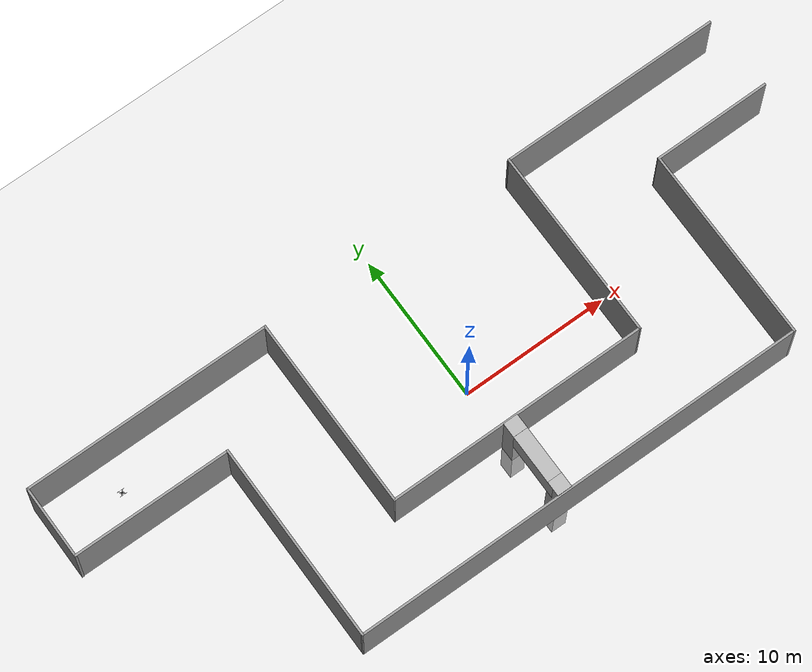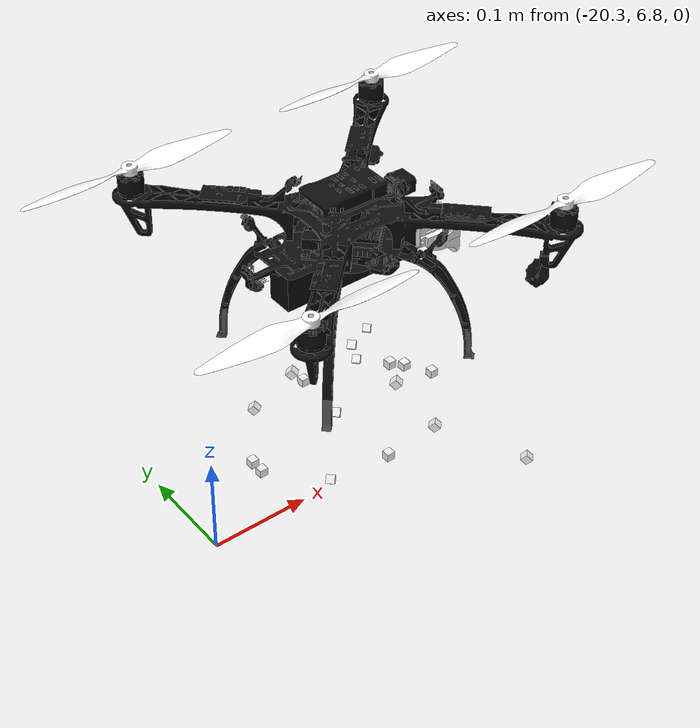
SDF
<sdf version='1.10'>
  <world name='hills'>
    <physics name='1ms' type='ignore'>
      <max_step_size>0.001</max_step_size>
      <real_time_factor>1</real_time_factor>
      <real_time_update_rate>1000</real_time_update_rate>
    </physics>
    <plugin name='gz::sim::systems::Physics' filename='gz-sim-physics-system'/>
    <plugin name='gz::sim::systems::Sensors' filename='gz-sim-sensors-system'>
      <render_engine>ogre2</render_engine>
    </plugin>
    <plugin name='gz::sim::systems::UserCommands' filename='gz-sim-user-commands-system'/>
    <plugin name='gz::sim::systems::SceneBroadcaster' filename='gz-sim-scene-broadcaster-system'/>
    <plugin name='gz::sim::systems::Imu' filename='gz-sim-imu-system'/>
    <plugin name='gz::sim::systems::NavSat' filename='gz-sim-navsat-system'/>
    <scene>
      <ambient>1 1 1 1</ambient>
      <background>0.800000012 0.800000012 0.800000012 1</background>
      <sky/>
      <shadows>true</shadows>
    </scene>
    <gravity>0 0 -9.8000000000000007</gravity>
    <magnetic_field>5.5644999999999998e-06 2.2875799999999999e-05 -4.2388400000000002e-05</magnetic_field>
    <atmosphere type='adiabatic'/>
    <model name='ground_plane'>
      <static>true</static>
      <link name='link'>
        <collision name='collision'>
          <geometry>
            <plane>
              <normal>0 0 1</normal>
              <size>100 100</size>
            </plane>
          </geometry>
          <surface>
            <friction>
              <ode/>
            </friction>
            <bounce/>
            <contact/>
          </surface>
        </collision>
        <visual name='visual'>
          <geometry>
            <plane>
              <normal>0 0 1</normal>
              <size>100 100</size>
            </plane>
          </geometry>
          <material>
            <ambient>0.800000012 0.800000012 0.800000012 1</ambient>
            <diffuse>0.800000012 0.800000012 0.800000012 1</diffuse>
            <specular>0.800000012 0.800000012 0.800000012 1</specular>
          </material>
        </visual>
        <pose>0 0 0 0 0 0</pose>
        <inertial>
          <pose>0 0 0 0 0 0</pose>
          <mass>1</mass>
          <inertia>
            <ixx>1</ixx>
            <ixy>0</ixy>
            <ixz>0</ixz>
            <iyy>1</iyy>
            <iyz>0</iyz>
            <izz>1</izz>
          </inertia>
        </inertial>
        <enable_wind>false</enable_wind>
      </link>
      <pose>0 0 0 0 0 0</pose>
      <self_collide>false</self_collide>
    </model>
    <include>
      <uri>file:///home/mebra06/ardupilot_gazebo/models/maze_model</uri>
      <name>maze_final2</name>
      <pose>5.3290705182007514e-15 1.3322676295501878e-15 0 0 0 0</pose>
    </include>
    <include>
      <uri>file:///home/mebra06/ardupilot_gazebo/models/kestrel_drone_lidar</uri>
      <name>kestrel_drone_lidar</name>
      <pose>-20.00000000788901 6.9999999605170693 -0.14400093308242207 1.2552848614890159e-08 1.4241819845697077e-09 -4.1022055614565063e-06</pose>
    </include>
    <model name='box'>
      <pose>0.26243729810331529 -4.3175410706887698 0.58844244308647076 -0.0083504758368533986 -0.00011937740155746955 1.0090674614620044e-06</pose>
      <link name='box_link'>
        <inertial>
          <inertia>
            <ixx>0.16666</ixx>
            <ixy>0</ixy>
            <ixz>0</ixz>
            <iyy>0.16666</iyy>
            <iyz>0</iyz>
            <izz>0.16666</izz>
          </inertia>
          <mass>1</mass>
          <pose>0 0 0 0 0 0</pose>
        </inertial>
        <collision name='box_collision'>
          <geometry>
            <box>
              <size>1 1 9</size>
            </box>
          </geometry>
          <surface>
            <friction>
              <ode/>
            </friction>
            <bounce/>
            <contact/>
          </surface>
        </collision>
        <visual name='box_visual'>
          <geometry>
            <box>
              <size>1 1 9</size>
            </box>
          </geometry>
          <material>
            <ambient>0.300000012 0.300000012 0.300000012 1</ambient>
            <diffuse>0.699999988 0.699999988 0.699999988 1</diffuse>
            <specular>1 1 1 1</specular>
          </material>
        </visual>
        <pose>0 0 0 0 0 0</pose>
        <enable_wind>false</enable_wind>
      </link>
      <static>false</static>
      <self_collide>false</self_collide>
    </model>
    <model name='box2'>
      <pose>0.26272119210684258 -8.5460158972626701 0.59220459440616025 0.0085375627009552976 -0.00010148629721059543 -0.0012948769855253665</pose>
      <link name='box_link'>
        <inertial>
          <inertia>
            <ixx>0.16666</ixx>
            <ixy>0</ixy>
            <ixz>0</ixz>
            <iyy>0.16666</iyy>
            <iyz>0</iyz>
            <izz>0.16666</izz>
          </inertia>
          <mass>1</mass>
          <pose>0 0 0 0 0 0</pose>
        </inertial>
        <collision name='box_collision'>
          <geometry>
            <box>
              <size>1 1 9</size>
            </box>
          </geometry>
          <surface>
            <friction>
              <ode/>
            </friction>
            <bounce/>
            <contact/>
          </surface>
        </collision>
        <visual name='box_visual'>
          <geometry>
            <box>
              <size>1 1 9</size>
            </box>
          </geometry>
          <material>
            <ambient>0.300000012 0.300000012 0.300000012 1</ambient>
            <diffuse>0.699999988 0.699999988 0.699999988 1</diffuse>
            <specular>1 1 1 1</specular>
          </material>
        </visual>
        <pose>0 0 0 0 0 0</pose>
        <enable_wind>false</enable_wind>
      </link>
      <static>false</static>
      <self_collide>false</self_collide>
    </model>
    <model name='box3'>
      <pose>0.26220520290636506 -6.5781585993273479 4.0799079637985702 0.00022984503071134152 -2.0055514732108337e-05 6.5835884052441758e-07</pose>
      <link name='box_link'>
        <inertial>
          <inertia>
            <ixx>0.16666</ixx>
            <ixy>0</ixy>
            <ixz>0</ixz>
            <iyy>0.16666</iyy>
            <iyz>0</iyz>
            <izz>0.16666</izz>
          </inertia>
          <mass>1</mass>
          <pose>0 0 0 0 0 0</pose>
        </inertial>
        <collision name='box_collision'>
          <geometry>
            <box>
              <size>1 4 2</size>
            </box>
          </geometry>
          <surface>
            <friction>
              <ode/>
            </friction>
            <bounce/>
            <contact/>
          </surface>
        </collision>
        <visual name='box_visual'>
          <geometry>
            <box>
              <size>1 4 2</size>
            </box>
          </geometry>
          <material>
            <ambient>0.300000012 0.300000012 0.300000012 1</ambient>
            <diffuse>0.699999988 0.699999988 0.699999988 1</diffuse>
            <specular>1 1 1 1</specular>
          </material>
        </visual>
        <pose>0 0 0 0 0 0</pose>
        <enable_wind>false</enable_wind>
      </link>
      <static>false</static>
      <self_collide>false</self_collide>
    </model>
    <light name='sun' type='directional'>
      <pose>0 0 10 0 0 0</pose>
      <cast_shadows>true</cast_shadows>
      <intensity>1</intensity>
      <direction>-0.5 0.10000000000000001 -0.90000000000000002</direction>
      <diffuse>0.800000012 0.800000012 0.800000012 1</diffuse>
      <specular>0.800000012 0.800000012 0.800000012 1</specular>
      <attenuation>
        <range>1000</range>
        <linear>0.0099999997764825821</linear>
        <constant>0.89999997615814209</constant>
        <quadratic>0.0010000000474974513</quadratic>
      </attenuation>
      <spot>
        <inner_angle>0</inner_angle>
        <outer_angle>0</outer_angle>
        <falloff>0</falloff>
      </spot>
    </light>
  </world>
</sdf>

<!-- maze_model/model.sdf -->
<sdf version='1.6'>
  <model name='maze_final2'>
    <pose frame=''>-0.943572 -1.95156 0 0 -0 0</pose>
    <link name='Wall_10'>
      <collision name='Wall_10_Collision'>
        <geometry>
          <box>
            <size>12.9601 0.15 5</size>
          </box>
        </geometry>
        <pose frame=''>0 0 2.5 0 -0 0</pose>
      </collision>
      <visual name='Wall_10_Visual'>
        <pose frame=''>0 0 2.5 0 -0 0</pose>
        <geometry>
          <box>
            <size>12.9601 0.15 5</size>
          </box>
        </geometry>
        <material>
          <script>
            <uri>file://media/materials/scripts/gazebo.material</uri>
            <name>Gazebo/Grey</name>
          </script>
          <ambient>1 1 1 1</ambient>
        </material>
      </visual>
      <pose frame=''>9.62007 2.65756 0 0 -0 1.574</pose>
    </link>
    <link name='Wall_11'>
      <collision name='Wall_11_Collision'>
        <geometry>
          <box>
            <size>15 0.15 5</size>
          </box>
        </geometry>
        <pose frame=''>0 0 2.5 0 -0 0</pose>
      </collision>
      <visual name='Wall_11_Visual'>
        <pose frame=''>0 0 2.5 0 -0 0</pose>
        <geometry>
          <box>
            <size>15 0.15 5</size>
          </box>
        </geometry>
        <material>
          <script>
            <uri>file://media/materials/scripts/gazebo.material</uri>
            <name>Gazebo/Grey</name>
          </script>
          <ambient>1 1 1 1</ambient>
        </material>
      </visual>
      <pose frame=''>17.0246 9.06206 0 0 0 -6.7e-05</pose>
    </link>
    <link name='Wall_13'>
      <collision name='Wall_13_Collision'>
        <geometry>
          <box>
            <size>5 0.15 5</size>
          </box>
        </geometry>
        <pose frame=''>0 0 2.5 0 -0 0</pose>
      </collision>
      <visual name='Wall_13_Visual'>
        <pose frame=''>0 0 2.5 0 -0 0</pose>
        <geometry>
          <box>
            <size>5 0.15 5</size>
          </box>
        </geometry>
        <material>
          <script>
            <uri>file://media/materials/scripts/gazebo.material</uri>
            <name>Gazebo/Grey</name>
          </script>
          <ambient>1 1 1 1</ambient>
        </material>
      </visual>
      <pose frame=''>-24.6999 6.67756 0 0 0 -1.5708</pose>
    </link>
    <link name='Wall_14'>
      <collision name='Wall_14_Collision'>
        <geometry>
          <box>
            <size>10.7524 0.15 5</size>
          </box>
        </geometry>
        <pose frame=''>0 0 2.5 0 -0 0</pose>
      </collision>
      <visual name='Wall_14_Visual'>
        <pose frame=''>0 0 2.5 0 -0 0</pose>
        <geometry>
          <box>
            <size>10.7524 0.15 5</size>
          </box>
        </geometry>
        <material>
          <script>
            <uri>file://media/materials/scripts/gazebo.material</uri>
            <name>Gazebo/Grey</name>
          </script>
          <ambient>1 1 1 1</ambient>
        </material>
      </visual>
      <pose frame=''>-19.3636 4.27015 0 0 0 -0.003318</pose>
    </link>
    <link name='Wall_15'>
      <collision name='Wall_15_Collision'>
        <geometry>
          <box>
            <size>13.5 0.15 5</size>
          </box>
        </geometry>
        <pose frame=''>0 0 2.5 0 -0 0</pose>
      </collision>
      <visual name='Wall_15_Visual'>
        <pose frame=''>0 0 2.5 0 -0 0</pose>
        <geometry>
          <box>
            <size>13.5 0.15 5</size>
          </box>
        </geometry>
        <material>
          <script>
            <uri>file://media/materials/scripts/gazebo.material</uri>
            <name>Gazebo/Grey</name>
          </script>
          <ambient>1 1 1 1</ambient>
        </material>
      </visual>
      <pose frame=''>-14.0619 -2.42244 0 0 0 -1.57072</pose>
    </link>
    <link name='Wall_16'>
      <collision name='Wall_16_Collision'>
        <geometry>
          <box>
            <size>31.0613 0.15 5</size>
          </box>
        </geometry>
        <pose frame=''>0 0 2.5 0 -0 0</pose>
      </collision>
      <visual name='Wall_16_Visual'>
        <pose frame=''>0 0 2.5 0 -0 0</pose>
        <geometry>
          <box>
            <size>31.0613 0.15 5</size>
          </box>
        </geometry>
        <material>
          <script>
            <uri>file://media/materials/scripts/gazebo.material</uri>
            <name>Gazebo/Grey</name>
          </script>
          <ambient>1 1 1 1</ambient>
        </material>
      </visual>
      <pose frame=''>1.39407 -9.11744 0 0 0 -0.001294</pose>
    </link>
    <link name='Wall_17'>
      <collision name='Wall_17_Collision'>
        <geometry>
          <box>
            <size>13.2499 0.15 5</size>
          </box>
        </geometry>
        <pose frame=''>0 0 2.5 0 -0 0</pose>
      </collision>
      <visual name='Wall_17_Visual'>
        <pose frame=''>0 0 2.5 0 -0 0</pose>
        <geometry>
          <box>
            <size>13.2499 0.15 5</size>
          </box>
        </geometry>
        <material>
          <script>
            <uri>file://media/materials/scripts/gazebo.material</uri>
            <name>Gazebo/Grey</name>
          </script>
          <ambient>1 1 1 1</ambient>
        </material>
      </visual>
      <pose frame=''>16.8496 -2.58794 0 0 -0 1.5708</pose>
    </link>
    <link name='Wall_18'>
      <collision name='Wall_18_Collision'>
        <geometry>
          <box>
            <size>8 0.15 5</size>
          </box>
        </geometry>
        <pose frame=''>0 0 2.5 0 -0 0</pose>
      </collision>
      <visual name='Wall_18_Visual'>
        <pose frame=''>0 0 2.5 0 -0 0</pose>
        <geometry>
          <box>
            <size>8 0.15 5</size>
          </box>
        </geometry>
        <material>
          <script>
            <uri>file://media/materials/scripts/gazebo.material</uri>
            <name>Gazebo/Grey</name>
          </script>
          <ambient>1 1 1 1</ambient>
        </material>
      </visual>
      <pose frame=''>20.7746 3.98206 0 0 -0 0.005223</pose>
    </link>
    <link name='Wall_7'>
      <collision name='Wall_7_Collision'>
        <geometry>
          <box>
            <size>16.8143 0.15 5</size>
          </box>
        </geometry>
        <pose frame=''>0 0 2.5 0 -0 0</pose>
      </collision>
      <visual name='Wall_7_Visual'>
        <pose frame=''>0 0 2.5 0 -0 0</pose>
        <geometry>
          <box>
            <size>16.8143 0.15 5</size>
          </box>
        </geometry>
        <material>
          <script>
            <uri>file://media/materials/scripts/gazebo.material</uri>
            <name>Gazebo/Grey</name>
          </script>
          <ambient>1 1 1 1</ambient>
        </material>
      </visual>
      <pose frame=''>-16.3326 9.12015 0 0 0 -0.002111</pose>
    </link>
    <link name='Wall_8'>
      <collision name='Wall_8_Collision'>
        <geometry>
          <box>
            <size>13 0.15 5</size>
          </box>
        </geometry>
        <pose frame=''>0 0 2.5 0 -0 0</pose>
      </collision>
      <visual name='Wall_8_Visual'>
        <pose frame=''>0 0 2.5 0 -0 0</pose>
        <geometry>
          <box>
            <size>13 0.15 5</size>
          </box>
        </geometry>
        <material>
          <script>
            <uri>file://media/materials/scripts/gazebo.material</uri>
            <name>Gazebo/Grey</name>
          </script>
          <ambient>1 1 1 1</ambient>
        </material>
      </visual>
      <pose frame=''>-7.98043 2.67756 0 0 0 -1.56768</pose>
    </link>
    <link name='Wall_9'>
      <collision name='Wall_9_Collision'>
        <geometry>
          <box>
            <size>17.7503 0.15 5</size>
          </box>
        </geometry>
        <pose frame=''>0 0 2.5 0 -0 0</pose>
      </collision>
      <visual name='Wall_9_Visual'>
        <pose frame=''>0 0 2.5 0 -0 0</pose>
        <geometry>
          <box>
            <size>17.7503 0.15 5</size>
          </box>
        </geometry>
        <material>
          <script>
            <uri>file://media/materials/scripts/gazebo.material</uri>
            <name>Gazebo/Grey</name>
          </script>
          <ambient>1 1 1 1</ambient>
        </material>
      </visual>
      <pose frame=''>0.840072 -3.74744 0 0 -0 0</pose>
    </link>
    <static>1</static>
  </model>
</sdf>

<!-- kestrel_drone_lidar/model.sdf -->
<sdf version="1.9">
    <model name='kestrel_drone_lidar'>
        <include>
            <uri>model://kestrel_drone</uri>
        </include>

        <!-- lidar 1: 45 down-forward-left  -->
        <link name="45dfl">
            <pose relative_to="45dfl-joint">0 0 0 0 0 0</pose>
            <inertial>
                <mass>0.1</mass>
                <inertia>
                    <ixx>0.000166667</ixx>
                    <iyy>0.000166667</iyy>
                    <izz>0.000166667</izz>
                </inertia>
            </inertial>
            <collision name="collision">
                <geometry>
                    <box>
                    <size>0.01 0.01 0.01</size>
                    </box>
                </geometry>
            </collision>
            <visual name="visual">
                <geometry>
                    <box>
                    <size>0.01 0.01 0.01</size>
                    </box>
                </geometry>
                <material>
                    <diffuse>1 1 1 0</diffuse>
                    <ambient>1 1 1 0</ambient>
                    <specular>1 1 1 0</specular>
                </material>
            </visual>
            <sensor name='gpu_lidar' type='gpu_lidar'>
                <topic>lidar/45dfl</topic>
                <update_rate>10</update_rate>
                <lidar>
                    <scan>
                    <horizontal>
                        <samples>640</samples>
                        <resolution>1</resolution>
                        <min_angle>-0.471239</min_angle>
                        <max_angle>0.471239</max_angle>
                    </horizontal>
                    <vertical>
                        <samples>16</samples>
                        <resolution>1</resolution>
                        <min_angle>-0.471239</min_angle>
                        <max_angle>0.471239</max_angle>
                    </vertical>
                    </scan>
                    <range>
                    <min>0.08</min>
                    <max>4.0</max>
                    <resolution>0.01</resolution>
                    </range>
                    <noise>
                        <type>gaussian</type>
                        <mean>0.0</mean>
                        <stddev>0.1</stddev>
                    </noise>
                </lidar>
                <visualize>true</visualize>
            </sensor>
        </link>
        <joint name="45dfl-joint" type="fixed">
            <pose relative_to="kestrel_drone::base_link">
                0.0739 0.0734 0 0 0.785398 0.785398
            </pose>
            <parent>kestrel_drone::base_link</parent>
            <child>45dfl</child>
        </joint>

        <!-- Lidar 2: forward -->
        <link name="forward">
            <pose relative_to="forward-joint">0 0 0 0 0 0</pose>
            <inertial>
                <mass>0.1</mass>
                <inertia>
                    <ixx>0.000166667</ixx>
                    <iyy>0.000166667</iyy>
                    <izz>0.000166667</izz>
                </inertia>
            </inertial>
            <collision name="collision">
                <geometry>
                    <box>
                    <size>0.01 0.01 0.01</size>
                    </box>
                </geometry>
            </collision>
            <visual name="visual">
                <geometry>
                    <box>
                    <size>0.01 0.01 0.01</size>
                    </box>
                </geometry>
                <material>
                    <diffuse>1 1 1 0</diffuse>
                    <ambient>1 1 1 0</ambient>
                    <specular>1 1 1 0</specular>
                </material>
            </visual>
            <sensor name='gpu_lidar' type='gpu_lidar'>
                <topic>lidar/forward</topic>
                <update_rate>10</update_rate>
                <lidar>
                    <scan>
                    <horizontal>
                        <samples>640</samples>
                        <resolution>1</resolution>
                        <min_angle>-0.471239</min_angle>
                        <max_angle>0.471239</max_angle>
                    </horizontal>
                    <vertical>
                        <samples>16</samples>
                        <resolution>1</resolution>
                        <min_angle>-0.471239</min_angle>
                        <max_angle>0.471239</max_angle>
                    </vertical>
                    </scan>
                    <range>
                    <min>0.08</min>
                    <max>4.0</max>
                    <resolution>0.01</resolution>
                    </range>
                    <noise>
                        <type>gaussian</type>
                        <mean>0.0</mean>
                        <stddev>0.1</stddev>
                    </noise>
                </lidar>
                <visualize>true</visualize>
            </sensor>
        </link>
        <joint name="forward-joint" type="fixed">
            <pose relative_to="kestrel_drone::base_link">
                0.1294	0.0004	0.0012 0 0 0
            </pose>
            <parent>kestrel_drone::base_link</parent>
            <child>forward</child>
        </joint>

        <!-- Lidar 3: 45 down-forward-right -->
        <link name="45dfr">
            <pose relative_to="45dfr-joint">0 0 0 0 0 0</pose>
            <inertial>
                <mass>0.1</mass>
                <inertia>
                    <ixx>0.000166667</ixx>
                    <iyy>0.000166667</iyy>
                    <izz>0.000166667</izz>
                </inertia>
            </inertial>
            <collision name="collision">
                <geometry>
                    <box>
                    <size>0.01 0.01 0.01</size>
                    </box>
                </geometry>
            </collision>
            <visual name="visual">
                <geometry>
                    <box>
                    <size>0.01 0.01 0.01</size>
                    </box>
                </geometry>
                <material>
                    <diffuse>1 1 1 0</diffuse>
                    <ambient>1 1 1 0</ambient>
                    <specular>1 1 1 0</specular>
                </material>
            </visual>
            <sensor name='gpu_lidar' type='gpu_lidar'>
                <topic>lidar/45dfr</topic>
                <update_rate>10</update_rate>
                <lidar>
                    <scan>
                    <horizontal>
                        <samples>640</samples>
                        <resolution>1</resolution>
                        <min_angle>-0.471239</min_angle>
                        <max_angle>0.471239</max_angle>
                    </horizontal>
                    <vertical>
                        <samples>16</samples>
                        <resolution>1</resolution>
                        <min_angle>-0.471239</min_angle>
                        <max_angle>0.471239</max_angle>
                    </vertical>
                    </scan>
                    <range>
                    <min>0.08</min>
                    <max>4.0</max>
                    <resolution>0.01</resolution>
                    </range>
                    <noise>
                        <type>gaussian</type>
                        <mean>0.0</mean>
                        <stddev>0.1</stddev>
                    </noise>
                </lidar>
                <visualize>true</visualize>
            </sensor>
        </link>
        <joint name="45dfr-joint" type="fixed">
            <pose relative_to="kestrel_drone::base_link">
                0.0730	-0.0735	0 0 0.785398 -0.785398
            </pose>
            <parent>kestrel_drone::base_link</parent>
            <child>45dfr</child>
        </joint>

        <!-- Lidar 4: Right -->
        <link name="right">
            <pose relative_to="right-joint">0 0 0 0 0 0</pose>
            <inertial>
                <mass>0.1</mass>
                <inertia>
                    <ixx>0.000166667</ixx>
                    <iyy>0.000166667</iyy>
                    <izz>0.000166667</izz>
                </inertia>
            </inertial>
            <collision name="collision">
                <geometry>
                    <box>
                    <size>0.01 0.01 0.01</size>
                    </box>
                </geometry>
            </collision>
            <visual name="visual">
                <geometry>
                    <box>
                    <size>0.01 0.01 0.01</size>
                    </box>
                </geometry>
                <material>
                    <diffuse>1 1 1 0</diffuse>
                    <ambient>1 1 1 0</ambient>
                    <specular>1 1 1 0</specular>
                </material>
            </visual>
            <sensor name='gpu_lidar' type='gpu_lidar'>
                <topic>lidar/right</topic>
                <update_rate>10</update_rate>
                <lidar>
                    <scan>
                    <horizontal>
                        <samples>640</samples>
                        <resolution>1</resolution>
                        <min_angle>-0.471239</min_angle>
                        <max_angle>0.471239</max_angle>
                    </horizontal>
                    <vertical>
                        <samples>16</samples>
                        <resolution>1</resolution>
                        <min_angle>-0.471239</min_angle>
                        <max_angle>0.471239</max_angle>
                    </vertical>
                    </scan>
                    <range>
                    <min>0.08</min>
                    <max>4.0</max>
                    <resolution>0.01</resolution>
                    </range>
                    <noise>
                        <type>gaussian</type>
                        <mean>0.0</mean>
                        <stddev>0.1</stddev>
                    </noise>
                </lidar>
                <visualize>true</visualize>
            </sensor>
        </link>
        <joint name="right-joint" type="fixed">
            <pose relative_to="kestrel_drone::base_link">
                0 -0.0810 0.0011 0 0 -1.570796
            </pose>
            <parent>kestrel_drone::base_link</parent>
            <child>right</child>
        </joint>

        <!-- Lidar 5: 45 down-rear-right -->
        <link name="45drr">
            <pose relative_to="45drr-joint">0 0 0 0 0 0</pose>
            <inertial>
                <mass>0.1</mass>
                <inertia>
                    <ixx>0.000166667</ixx>
                    <iyy>0.000166667</iyy>
                    <izz>0.000166667</izz>
                </inertia>
            </inertial>
            <collision name="collision">
                <geometry>
                    <box>
                    <size>0.01 0.01 0.01</size>
                    </box>
                </geometry>
            </collision>
            <visual name="visual">
                <geometry>
                    <box>
                    <size>0.01 0.01 0.01</size>
                    </box>
                </geometry>
                <material>
                    <diffuse>1 1 1 0</diffuse>
                    <ambient>1 1 1 0</ambient>
                    <specular>1 1 1 0</specular>
                </material>
            </visual>
            <sensor name='gpu_lidar' type='gpu_lidar'>
                <topic>lidar/45drr</topic>
                <update_rate>10</update_rate>
                <lidar>
                    <scan>
                    <horizontal>
                        <samples>640</samples>
                        <resolution>1</resolution>
                        <min_angle>-0.471239</min_angle>
                        <max_angle>0.471239</max_angle>
                    </horizontal>
                    <vertical>
                        <samples>16</samples>
                        <resolution>1</resolution>
                        <min_angle>-0.471239</min_angle>
                        <max_angle>0.471239</max_angle>
                    </vertical>
                    </scan>
                    <range>
                    <min>0.08</min>
                    <max>4.0</max>
                    <resolution>0.01</resolution>
                    </range>
                    <noise>
                        <type>gaussian</type>
                        <mean>0.0</mean>
                        <stddev>0.1</stddev>
                    </noise>
                </lidar>
                <visualize>true</visualize>
            </sensor>
        </link>
        <joint name="45drr-joint" type="fixed">
            <pose relative_to="kestrel_drone::base_link">
                -0.0739	-0.0726	0 0 2.35619 0.785398
            </pose>
            <parent>kestrel_drone::base_link</parent>
            <child>45drr</child>
        </joint>

        <!-- Lidar 6: Rear -->
        <link name="rear">
            <pose relative_to="rear-joint">0 0 0 0 0 0</pose>
            <inertial>
                <mass>0.1</mass>
                <inertia>
                    <ixx>0.000166667</ixx>
                    <iyy>0.000166667</iyy>
                    <izz>0.000166667</izz>
                </inertia>
            </inertial>
            <collision name="collision">
                <geometry>
                    <box>
                    <size>0.01 0.01 0.01</size>
                    </box>
                </geometry>
            </collision>
            <visual name="visual">
                <geometry>
                    <box>
                    <size>0.01 0.01 0.01</size>
                    </box>
                </geometry>
                <material>
                    <diffuse>1 1 1 0</diffuse>
                    <ambient>1 1 1 0</ambient>
                    <specular>1 1 1 0</specular>
                </material>
            </visual>
            <sensor name='gpu_lidar' type='gpu_lidar'>
                <topic>lidar/rear</topic>
                <update_rate>10</update_rate>
                <lidar>
                    <scan>
                    <horizontal>
                        <samples>640</samples>
                        <resolution>1</resolution>
                        <min_angle>-0.471239</min_angle>
                        <max_angle>0.471239</max_angle>
                    </horizontal>
                    <vertical>
                        <samples>16</samples>
                        <resolution>1</resolution>
                        <min_angle>-0.471239</min_angle>
                        <max_angle>0.471239</max_angle>
                    </vertical>
                    </scan>
                    <range>
                    <min>0.08</min>
                    <max>4.0</max>
                    <resolution>0.01</resolution>
                    </range>
                    <noise>
                        <type>gaussian</type>
                        <mean>0.0</mean>
                        <stddev>0.1</stddev>
                    </noise>
                </lidar>
                <visualize>true</visualize>
            </sensor>
        </link>
        <joint name="rear-joint" type="fixed">
            <pose relative_to="kestrel_drone::base_link">
                -0.1264	0.0004	0.0012 0 0 3.14159
            </pose>
            <parent>kestrel_drone::base_link</parent>
            <child>rear</child>
        </joint>

        <!-- Lidar 7: 45 down-rear-left -->
        <link name="45drl">
            <pose relative_to="45drl-joint">0 0 0 0 0 0</pose>
            <inertial>
                <mass>0.1</mass>
                <inertia>
                    <ixx>0.000166667</ixx>
                    <iyy>0.000166667</iyy>
                    <izz>0.000166667</izz>
                </inertia>
            </inertial>
            <collision name="collision">
                <geometry>
                    <box>
                    <size>0.01 0.01 0.01</size>
                    </box>
                </geometry>
            </collision>
            <visual name="visual">
                <geometry>
                    <box>
                    <size>0.01 0.01 0.01</size>
                    </box>
                </geometry>
                <material>
                    <diffuse>1 1 1 0</diffuse>
                    <ambient>1 1 1 0</ambient>
                    <specular>1 1 1 0</specular>
                </material>
            </visual>
            <sensor name='gpu_lidar' type='gpu_lidar'>
                <topic>lidar/45drl</topic>
                <update_rate>10</update_rate>
                <lidar>
                    <scan>
                    <horizontal>
                        <samples>640</samples>
                        <resolution>1</resolution>
                        <min_angle>-0.471239</min_angle>
                        <max_angle>0.471239</max_angle>
                    </horizontal>
                    <vertical>
                        <samples>16</samples>
                        <resolution>1</resolution>
                        <min_angle>-0.471239</min_angle>
                        <max_angle>0.471239</max_angle>
                    </vertical>
                    </scan>
                    <range>
                    <min>0.08</min>
                    <max>4.0</max>
                    <resolution>0.01</resolution>
                    </range>
                    <noise>
                        <type>gaussian</type>
                        <mean>0.0</mean>
                        <stddev>0.1</stddev>
                    </noise>
                </lidar>
                <visualize>true</visualize>
            </sensor>
        </link>
        <joint name="45drl-joint" type="fixed">
            <pose relative_to="kestrel_drone::base_link">
                -0.0730	0.0743	0 0 2.35619 -0.785398
            </pose>
            <parent>kestrel_drone::base_link</parent>
            <child>45drl</child>
        </joint>

        <!-- Lidar 8: Left -->
        <link name="left">
            <pose relative_to="left-joint">0 0 0 0 0 0</pose>
            <inertial>
                <mass>0.1</mass>
                <inertia>
                    <ixx>0.000166667</ixx>
                    <iyy>0.000166667</iyy>
                    <izz>0.000166667</izz>
                </inertia>
            </inertial>
            <collision name="collision">
                <geometry>
                    <box>
                    <size>0.01 0.01 0.01</size>
                    </box>
                </geometry>
            </collision>
            <visual name="visual">
                <geometry>
                    <box>
                    <size>0.01 0.01 0.01</size>
                    </box>
                </geometry>
                <material>
                    <diffuse>1 1 1 0</diffuse>
                    <ambient>1 1 1 0</ambient>
                    <specular>1 1 1 0</specular>
                </material>
            </visual>
            <sensor name='gpu_lidar' type='gpu_lidar'>
                <topic>lidar/left</topic>
                <update_rate>10</update_rate>
                <lidar>
                    <scan>
                    <horizontal>
                        <samples>640</samples>
                        <resolution>1</resolution>
                        <min_angle>-0.471239</min_angle>
                        <max_angle>0.471239</max_angle>
                    </horizontal>
                    <vertical>
                        <samples>16</samples>
                        <resolution>1</resolution>
                        <min_angle>-0.471239</min_angle>
                        <max_angle>0.471239</max_angle>
                    </vertical>
                    </scan>
                    <range>
                    <min>0.08</min>
                    <max>4.0</max>
                    <resolution>0.01</resolution>
                    </range>
                    <noise>
                        <type>gaussian</type>
                        <mean>0.0</mean>
                        <stddev>0.1</stddev>
                    </noise>
                </lidar>
                <visualize>true</visualize>
            </sensor>
        </link>
        <joint name="left-joint" type="fixed">
            <pose relative_to="kestrel_drone::base_link">
                0.0000	0.0789	0.0011 0 0 1.570796
            </pose>
            <parent>kestrel_drone::base_link</parent>
            <child>left</child>
        </joint>

        <!-- Lidar 9: Down -->
        <link name="down">
            <pose relative_to="down-joint">0 0 0 0 0 0</pose>
            <inertial>
                <mass>0.1</mass>
                <inertia>
                    <ixx>0.000166667</ixx>
                    <iyy>0.000166667</iyy>
                    <izz>0.000166667</izz>
                </inertia>
            </inertial>
            <collision name="collision">
                <geometry>
                    <box>
                    <size>0.01 0.01 0.01</size>
                    </box>
                </geometry>
            </collision>
            <visual name="visual">
                <geometry>
                    <box>
                    <size>0.01 0.01 0.01</size>
                    </box>
                </geometry>
                <material>
                    <diffuse>1 1 1 0</diffuse>
                    <ambient>1 1 1 0</ambient>
                    <specular>1 1 1 0</specular>
                </material>
            </visual>
            <sensor name='gpu_lidar' type='gpu_lidar'>
                <topic>lidar/down</topic>
                <update_rate>10</update_rate>
                <lidar>
                    <scan>
                    <horizontal>
                        <samples>640</samples>
                        <resolution>1</resolution>
                        <min_angle>-0.471239</min_angle>
                        <max_angle>0.471239</max_angle>
                    </horizontal>
                    <vertical>
                        <samples>16</samples>
                        <resolution>1</resolution>
                        <min_angle>-0.471239</min_angle>
                        <max_angle>0.471239</max_angle>
                    </vertical>
                    </scan>
                    <range>
                    <min>0.08</min>
                    <max>4.0</max>
                    <resolution>0.01</resolution>
                    </range>
                    <noise>
                        <type>gaussian</type>
                        <mean>0.0</mean>
                        <stddev>0.1</stddev>
                    </noise>
                </lidar>
                <visualize>true</visualize>
            </sensor>
        </link>
        <joint name="down-joint" type="fixed">
            <pose relative_to="kestrel_drone::base_link">
                -0.1154	0.0004	-0.0186 0 1.5708 0
            </pose>
            <parent>kestrel_drone::base_link</parent>
            <child>down</child>
        </joint>

        <!-- Lidar 10: 45 up-forward-right -->
        <link name="45ufr">
            <pose relative_to="45ufr-joint">0 0 0 0 0 0</pose>
            <inertial>
                <mass>0.1</mass>
                <inertia>
                    <ixx>0.000166667</ixx>
                    <iyy>0.000166667</iyy>
                    <izz>0.000166667</izz>
                </inertia>
            </inertial>
            <collision name="collision">
                <geometry>
                    <box>
                    <size>0.01 0.01 0.01</size>
                    </box>
                </geometry>
            </collision>
            <visual name="visual">
                <geometry>
                    <box>
                    <size>0.01 0.01 0.01</size>
                    </box>
                </geometry>
                <material>
                    <diffuse>1 1 1 0</diffuse>
                    <ambient>1 1 1 0</ambient>
                    <specular>1 1 1 0</specular>
                </material>
            </visual>
            <sensor name='gpu_lidar' type='gpu_lidar'>
                <topic>lidar/45ufr</topic>
                <update_rate>10</update_rate>
                <lidar>
                    <scan>
                    <horizontal>
                        <samples>640</samples>
                        <resolution>1</resolution>
                        <min_angle>-0.471239</min_angle>
                        <max_angle>0.471239</max_angle>
                    </horizontal>
                    <vertical>
                        <samples>16</samples>
                        <resolution>1</resolution>
                        <min_angle>-0.471239</min_angle>
                        <max_angle>0.471239</max_angle>
                    </vertical>
                    </scan>
                    <range>
                    <min>0.08</min>
                    <max>4.0</max>
                    <resolution>0.01</resolution>
                    </range>
                    <noise>
                        <type>gaussian</type>
                        <mean>0.0</mean>
                        <stddev>0.1</stddev>
                    </noise>
                </lidar>
                <visualize>true</visualize>
            </sensor>
        </link>
        <joint name="45ufr-joint" type="fixed">
            <pose relative_to="kestrel_drone::base_link">
                0.0411	-0.0415	0.0580 0 -0.785398 -0.785398
            </pose>
            <parent>kestrel_drone::base_link</parent>
            <child>45ufr</child>
        </joint>

        <!-- Lidar 11: Up -->
        <link name="up">
            <pose relative_to="up-joint">0 0 0 0 0 0</pose>
            <inertial>
                <mass>0.1</mass>
                <inertia>
                    <ixx>0.000166667</ixx>
                    <iyy>0.000166667</iyy>
                    <izz>0.000166667</izz>
                </inertia>
            </inertial>
            <collision name="collision">
                <geometry>
                    <box>
                    <size>0.01 0.01 0.01</size>
                    </box>
                </geometry>
            </collision>
            <visual name="visual">
                <geometry>
                    <box>
                    <size>0.01 0.01 0.01</size>
                    </box>
                </geometry>
                <material>
                    <diffuse>1 1 1 0</diffuse>
                    <ambient>1 1 1 0</ambient>
                    <specular>1 1 1 0</specular>
                </material>
            </visual>
            <sensor name='gpu_lidar' type='gpu_lidar'>
                <topic>lidar/up</topic>
                <update_rate>10</update_rate>
                <lidar>
                    <scan>
                    <horizontal>
                        <samples>640</samples>
                        <resolution>1</resolution>
                        <min_angle>-0.471239</min_angle>
                        <max_angle>0.471239</max_angle>
                    </horizontal>
                    <vertical>
                        <samples>16</samples>
                        <resolution>1</resolution>
                        <min_angle>-0.471239</min_angle>
                        <max_angle>0.471239</max_angle>
                    </vertical>
                    </scan>
                    <range>
                    <min>0.08</min>
                    <max>4.0</max>
                    <resolution>0.01</resolution>
                    </range>
                    <noise>
                        <type>gaussian</type>
                        <mean>0.0</mean>
                        <stddev>0.1</stddev>
                    </noise>
                </lidar>
                <visualize>true</visualize>
            </sensor>
        </link>
        <joint name="up-joint" type="fixed">
            <pose relative_to="kestrel_drone::base_link">
                0.0653 -0.0001 0.0466 0 -1.5708 0
            </pose>
            <parent>kestrel_drone::base_link</parent>
            <child>up</child>
        </joint>

        <!-- Lidar 12: 45 up-forward-left -->
        <link name="45ufl">
            <pose relative_to="45ufl-joint">0 0 0 0 0 0</pose>
            <inertial>
                <mass>0.1</mass>
                <inertia>
                    <ixx>0.000166667</ixx>
                    <iyy>0.000166667</iyy>
                    <izz>0.000166667</izz>
                </inertia>
            </inertial>
            <collision name="collision">
                <geometry>
                    <box>
                    <size>0.01 0.01 0.01</size>
                    </box>
                </geometry>
            </collision>
            <visual name="visual">
                <geometry>
                    <box>
                    <size>0.01 0.01 0.01</size>
                    </box>
                </geometry>
                <material>
                    <diffuse>1 1 1 0</diffuse>
                    <ambient>1 1 1 0</ambient>
                    <specular>1 1 1 0</specular>
                </material>
            </visual>
            <sensor name='gpu_lidar' type='gpu_lidar'>
                <topic>lidar/45ufl</topic>
                <update_rate>10</update_rate>
                <lidar>
                    <scan>
                    <horizontal>
                        <samples>640</samples>
                        <resolution>1</resolution>
                        <min_angle>-0.471239</min_angle>
                        <max_angle>0.471239</max_angle>
                    </horizontal>
                    <vertical>
                        <samples>16</samples>
                        <resolution>1</resolution>
                        <min_angle>-0.471239</min_angle>
                        <max_angle>0.471239</max_angle>
                    </vertical>
                    </scan>
                    <range>
                    <min>0.08</min>
                    <max>4.0</max>
                    <resolution>0.01</resolution>
                    </range>
                    <noise>
                        <type>gaussian</type>
                        <mean>0.0</mean>
                        <stddev>0.1</stddev>
                    </noise>
                </lidar>
                <visualize>true</visualize>
            </sensor>
        </link>
        <joint name="45ufl-joint" type="fixed">
            <pose relative_to="kestrel_drone::base_link">
                0.0424	0.0415	0.0580 0 -0.785398 0.785398
            </pose>
            <parent>kestrel_drone::base_link</parent>
            <child>45ufl</child>
        </joint>

        <!-- Lidar 13: 45 up-rear-left -->
        <link name="45url">
            <pose relative_to="45url-joint">0 0 0 0 0 0</pose>
            <inertial>
                <mass>0.1</mass>
                <inertia>
                    <ixx>0.000166667</ixx>
                    <iyy>0.000166667</iyy>
                    <izz>0.000166667</izz>
                </inertia>
            </inertial>
            <collision name="collision">
                <geometry>
                    <box>
                    <size>0.01 0.01 0.01</size>
                    </box>
                </geometry>
            </collision>
            <visual name="visual">
                <geometry>
                    <box>
                    <size>0.01 0.01 0.01</size>
                    </box>
                </geometry>
                <material>
                    <diffuse>1 1 1 0</diffuse>
                    <ambient>1 1 1 0</ambient>
                    <specular>1 1 1 0</specular>
                </material>
            </visual>
            <sensor name='gpu_lidar' type='gpu_lidar'>
                <topic>lidar/45url</topic>
                <update_rate>10</update_rate>
                <lidar>
                    <scan>
                    <horizontal>
                        <samples>640</samples>
                        <resolution>1</resolution>
                        <min_angle>-0.471239</min_angle>
                        <max_angle>0.471239</max_angle>
                    </horizontal>
                    <vertical>
                        <samples>16</samples>
                        <resolution>1</resolution>
                        <min_angle>-0.471239</min_angle>
                        <max_angle>0.471239</max_angle>
                    </vertical>
                    </scan>
                    <range>
                    <min>0.08</min>
                    <max>4.0</max>
                    <resolution>0.01</resolution>
                    </range>
                    <noise>
                        <type>gaussian</type>
                        <mean>0.0</mean>
                        <stddev>0.1</stddev>
                    </noise>
                </lidar>
                <visualize>true</visualize>
            </sensor>
        </link>
        <joint name="45url-joint" type="fixed">
            <pose relative_to="kestrel_drone::base_link">
                -0.0411	0.0429	0.0580 0 -2.35619 -0.785398
            </pose>
            <parent>kestrel_drone::base_link</parent>
            <child>45url</child>
        </joint>

        <!-- Lidar 14: 45 up-rear-right -->
        <link name="45urr">
            <pose relative_to="45urr-joint">0 0 0 0 0 0</pose>
            <inertial>
                <mass>0.1</mass>
                <inertia>
                    <ixx>0.000166667</ixx>
                    <iyy>0.000166667</iyy>
                    <izz>0.000166667</izz>
                </inertia>
            </inertial>
            <collision name="collision">
                <geometry>
                    <box>
                    <size>0.01 0.01 0.01</size>
                    </box>
                </geometry>
            </collision>
            <visual name="visual">
                <geometry>
                    <box>
                    <size>0.01 0.01 0.01</size>
                    </box>
                </geometry>
                <material>
                    <diffuse>1 1 1 0</diffuse>
                    <ambient>1 1 1 0</ambient>
                    <specular>1 1 1 0</specular>
                </material>
            </visual>
            <sensor name='gpu_lidar' type='gpu_lidar'>
                <topic>lidar/45urr</topic>
                <update_rate>10</update_rate>
                <lidar>
                    <scan>
                    <horizontal>
                        <samples>640</samples>
                        <resolution>1</resolution>
                        <min_angle>-0.471239</min_angle>
                        <max_angle>0.471239</max_angle>
                    </horizontal>
                    <vertical>
                        <samples>16</samples>
                        <resolution>1</resolution>
                        <min_angle>-0.471239</min_angle>
                        <max_angle>0.471239</max_angle>
                    </vertical>
                    </scan>
                    <range>
                    <min>0.08</min>
                    <max>4.0</max>
                    <resolution>0.01</resolution>
                    </range>
                    <noise>
                        <type>gaussian</type>
                        <mean>0.0</mean>
                        <stddev>0.1</stddev>
                    </noise>
                </lidar>
                <visualize>true</visualize>
            </sensor>
        </link>
        <joint name="45urr-joint" type="fixed">
            <pose relative_to="kestrel_drone::base_link">
                -0.0424	-0.0406	0.0580 0 -2.35619 0.785398
            </pose>
            <parent>kestrel_drone::base_link</parent>
            <child>45urr</child>
        </joint>

        <!-- Lidar 15: Forward long range -->
        <link name="forwardl">
            <pose relative_to="forwardl-joint">0 0 0 0 0 0</pose>
            <inertial>
                <mass>0.1</mass>
                <inertia>
                    <ixx>0.000166667</ixx>
                    <iyy>0.000166667</iyy>
                    <izz>0.000166667</izz>
                </inertia>
            </inertial>
            <collision name="collision">
                <geometry>
                    <box>
                    <size>0.01 0.01 0.01</size>
                    </box>
                </geometry>
            </collision>
            <visual name="visual">
                <geometry>
                    <box>
                    <size>0.01 0.01 0.01</size>
                    </box>
                </geometry>
                <material>
                    <diffuse>1 1 1 0</diffuse>
                    <ambient>1 1 1 0</ambient>
                    <specular>1 1 1 0</specular>
                </material>
            </visual>
            <sensor name='gpu_lidar' type='gpu_lidar'>
                <topic>lidar/forwardl</topic>
                <update_rate>10</update_rate>
                <lidar>
                    <scan>
                    <horizontal>
                        <samples>640</samples>
                        <resolution>1</resolution>
                        <min_angle>-0.0349066</min_angle>
                        <max_angle>0.0349066</max_angle>
                    </horizontal>
                    <vertical>
                        <samples>16</samples>
                        <resolution>1</resolution>
                        <min_angle>-0.0349066</min_angle>
                        <max_angle>0.0349066</max_angle>
                    </vertical>
                    </scan>
                    <range>
                    <min>0.08</min>
                    <max>8.0</max>
                    <resolution>0.01</resolution>
                    </range>
                    <noise>
                        <type>gaussian</type>
                        <mean>0.0</mean>
                        <stddev>0.1</stddev>
                    </noise>
                </lidar>
                <visualize>true</visualize>
            </sensor>
        </link>
        <joint name="forwardl-joint" type="fixed">
            <pose relative_to="kestrel_drone::base_link">
                0.0866	-0.0001	0.0339 0 0 0
            </pose>
            <parent>kestrel_drone::base_link</parent>
            <child>forwardl</child>
        </joint>

        <!-- Lidar 16: 45 down-forward-right(long) -->
        <link name="45dfrl">
            <pose relative_to="45dfrl-joint">0 0 0 0 0 0</pose>
            <inertial>
                <mass>0.1</mass>
                <inertia>
                    <ixx>0.000166667</ixx>
                    <iyy>0.000166667</iyy>
                    <izz>0.000166667</izz>
                </inertia>
            </inertial>
            <collision name="collision">
                <geometry>
                    <box>
                    <size>0.01 0.01 0.01</size>
                    </box>
                </geometry>
            </collision>
            <visual name="visual">
                <geometry>
                    <box>
                    <size>0.01 0.01 0.01</size>
                    </box>
                </geometry>
                <material>
                    <diffuse>1 1 1 0</diffuse>
                    <ambient>1 1 1 0</ambient>
                    <specular>1 1 1 0</specular>
                </material>
            </visual>
            <sensor name='gpu_lidar' type='gpu_lidar'>
                <topic>lidar/45dfrl</topic>
                <update_rate>10</update_rate>
                <lidar>
                    <scan>
                    <horizontal>
                        <samples>640</samples>
                        <resolution>1</resolution>
                        <min_angle>-0.0349066</min_angle>
                        <max_angle>0.0349066</max_angle>
                    </horizontal>
                    <vertical>
                        <samples>16</samples>
                        <resolution>1</resolution>
                        <min_angle>-0.0349066</min_angle>
                        <max_angle>0.0349066</max_angle>
                    </vertical>
                    </scan>
                    <range>
                    <min>0.08</min>
                    <max>8.0</max>
                    <resolution>0.01</resolution>
                    </range>
                    <noise>
                        <type>gaussian</type>
                        <mean>0.0</mean>
                        <stddev>0.1</stddev>
                    </noise>
                </lidar>
                <visualize>true</visualize>
            </sensor>
        </link>
        <joint name="45dfrl-joint" type="fixed">
            <pose relative_to="kestrel_drone::base_link">
               0.1482	-0.1484	-0.0366 0 0.785398 -0.785398
            </pose>
            <parent>kestrel_drone::base_link</parent>
            <child>45dfrl</child>
        </joint>

        <!-- Lidar 16: 45 down-forward-left(long) -->
        <link name="45dfrll">
            <pose relative_to="45dfrll-joint">0 0 0 0 0 0</pose>
            <inertial>
                <mass>0.1</mass>
                <inertia>
                    <ixx>0.000166667</ixx>
                    <iyy>0.000166667</iyy>
                    <izz>0.000166667</izz>
                </inertia>
            </inertial>
            <collision name="collision">
                <geometry>
                    <box>
                    <size>0.01 0.01 0.01</size>
                    </box>
                </geometry>
            </collision>
            <visual name="visual">
                <geometry>
                    <box>
                    <size>0.01 0.01 0.01</size>
                    </box>
                </geometry>
                <material>
                    <diffuse>1 1 1 0</diffuse>
                    <ambient>1 1 1 0</ambient>
                    <specular>1 1 1 0</specular>
                </material>
            </visual>
            <sensor name='gpu_lidar' type='gpu_lidar'>
                <topic>lidar/45dfrll</topic>
                <update_rate>10</update_rate>
                <lidar>
                    <scan>
                    <horizontal>
                        <samples>640</samples>
                        <resolution>1</resolution>
                        <min_angle>-0.0349066</min_angle>
                        <max_angle>0.0349066</max_angle>
                    </horizontal>
                    <vertical>
                        <samples>16</samples>
                        <resolution>1</resolution>
                        <min_angle>-0.0349066</min_angle>
                        <max_angle>0.0349066</max_angle>
                    </vertical>
                    </scan>
                    <range>
                    <min>0.08</min>
                    <max>8.0</max>
                    <resolution>0.01</resolution>
                    </range>
                    <noise>
                        <type>gaussian</type>
                        <mean>0.0</mean>
                        <stddev>0.1</stddev>
                    </noise>
                </lidar>
                <visualize>true</visualize>
            </sensor>
        </link>
        <joint name="45dfrll-joint" type="fixed">
            <pose relative_to="kestrel_drone::base_link">
               0.1488	0.1487	-0.0366 0 0.785398 0.785398
            </pose>
            <parent>kestrel_drone::base_link</parent>
            <child>45dfrll</child>
        </joint>

    </model>
</sdf>

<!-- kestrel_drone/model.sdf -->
<sdf version="1.9">
    <model name='kestrel_drone'>
        <pose>0 0 0.25 0 0 0</pose>
        <link name='base_link'>
        <velocity_decay>
            <linear>0.0</linear>
            <angular>0.0</angular>
        </velocity_decay>
        <inertial>
            <pose>0.008 -0.0003 0.006 0 0 0</pose>
            <mass>1.6</mass>
            <inertia>
            <ixx>0.0055</ixx>
            <ixy>0</ixy>
            <ixz>0</ixz>
            <iyy>0.0067</iyy>
            <iyz>0</iyz>
            <izz>0.0099</izz>
            </inertia>
        </inertial>
        <collision name='base_link_collision'>
            <pose>0 0 0 0 0 0</pose>
            <geometry>
            <box>
                <size>0.358541 0.358541 0.212</size>
            </box>
            </geometry>
            <surface>
            <contact>
                <ode>
                <max_vel>100.0</max_vel>
                <min_depth>0.001</min_depth>
                </ode>
            </contact>
            <friction>
                <ode>
                <mu>100000.0</mu>
                <mu2>100000.0</mu2>
                </ode>
            </friction>
            </surface>
        </collision>
        <visual name='base_link_visual'>
            <pose>0 0 0 0 0 0</pose>
            <geometry>
                <mesh>
                    <scale>1 1 1</scale>
                    <uri>model://kestrel_drone/meshes/base_link.STL</uri>
                </mesh>
            </geometry>
            <material>
                <ambient>0.05 0.05 0.05</ambient>
                <diffuse>0.05 0.05 0.05</diffuse>
                <specular>1 1 1 1</specular>
                <pbr>
                    <metal>
                        <metalness>0.5</metalness>
                        <roughness>0.5</roughness>
                    </metal>
                </pbr>
            </material>
        </visual>
        </link>
        <joint name='CameraPt1-joint' type='revolute'>
        <pose relative_to='base_link'>0.1087 0 -0.051799999999999999 0 0 -0.016688999999999996</pose>
        <parent>base_link</parent>
        <child>CameraPt1</child>
        <axis>
            <xyz>0 0 1</xyz>
            <limit>
            <effort>1.4710000000000001</effort>
            <velocity>5.2359999999999998</velocity>
            <lower>0</lower>
            <upper>3.1415</upper>
            </limit>
            <dynamics>
                <spring_reference>0</spring_reference>
                <spring_stiffness>0</spring_stiffness>
            </dynamics>
        </axis>
        </joint>
        <link name='CameraPt1'>
        <pose relative_to='CameraPt1-joint'>0 0 0 0 0 0</pose>
        <inertial>
            <pose>-0.10077 -0.0019816999999999999 0.058075000000000002 0 0 0</pose>
            <mass>0.01</mass>
            <inertia>
            <ixx>0.0054891000000000002</ixx>
            <ixy>-1.2663000000000001e-05</ixy>
            <ixz>0.00018552999999999999</ixz>
            <iyy>0.0066689999999999996</iyy>
            <iyz>1.8978000000000001e-06</iyz>
            <izz>0.0098706999999999996</izz>
            </inertia>
        </inertial>
        <collision name='CameraPt1_collision'>
            <pose>0 0 0 0 0 0</pose>
            <geometry>
            <mesh>
                <scale>1 1 1</scale>
                <uri>model://kestrel_drone/meshes/CameraPt1.STL</uri>
            </mesh>
            </geometry>
        </collision>
        <visual name='CameraPt1_visual'>
            <pose>0 0 0 0 0 0</pose>
            <geometry>
            <mesh>
                <scale>1 1 1</scale>
                <uri>model://kestrel_drone/meshes/CameraPt1.STL</uri>
            </mesh>
            </geometry>
            <material>
                <diffuse>1 1 1 1</diffuse>
                <ambient>1 1 1 1</ambient>
                <pbr>
                    <metal>
                        <metalness>0.5</metalness>
                        <roughness>0.5</roughness>
                    </metal>
                </pbr>
            </material>
        </visual>
        </link>
        <joint name='CameraPt2-joint' type='revolute'>
        <pose relative_to='CameraPt1'>0.011849999999999999 0 0.0079000000000000008 0 0.0053803999999999996 0</pose>
        <parent>CameraPt1</parent>
        <child>CameraPt2</child>
        <axis>
            <xyz>0 -1 0</xyz>
            <limit>
            <effort>1.571</effort>
            <velocity>5.236</velocity>
            <lower>-1.5708</lower>
            <upper>0</upper>
            </limit>
            <dynamics>
            <spring_reference>0</spring_reference>
            <spring_stiffness>0</spring_stiffness>
            </dynamics>
        </axis>
        </joint>
        <link name='CameraPt2'>
        <pose relative_to='CameraPt2-joint'>0 0 0 0 0 0</pose>
        <inertial>
            <pose>-0.11289 -0.0019816999999999999 0.049568000000000001 0 0 0</pose>
            <mass>0.01</mass>
            <inertia>
            <ixx>0.0054872000000000002</ixx>
            <ixy>-1.2673e-05</ixy>
            <ixz>0.00016194000000000001</ixz>
            <iyy>0.0066689999999999996</iyy>
            <iyz>1.8296e-06</iyz>
            <izz>0.0098724999999999993</izz>
            </inertia>
        </inertial>
        <collision name='CameraPt2_collision'>
            <pose>0 0 0 0 0 0</pose>
            <geometry>
            <mesh>
                <scale>1 1 1</scale>
                <uri>model://kestrel_drone/meshes/CameraPt2.STL</uri>
            </mesh>
            </geometry>
        </collision>
        <visual name='CameraPt2_visual'>
            <pose>0 0 0 0 0 0</pose>
            <geometry>
            <mesh>
                <scale>1 1 1</scale>
                <uri>model://kestrel_drone/meshes/CameraPt2.STL</uri>
            </mesh>
            </geometry>
            <material>
                <diffuse>1 1 1 1</diffuse>
                <ambient>1 1 1 1</ambient>
                <pbr>
                    <metal>
                        <metalness>0.5</metalness>
                        <roughness>0.5</roughness>
                    </metal>
                </pbr>
            </material>
        </visual>
        <sensor name="camera" type="camera">
            <pose>0 0 0 0 0 0</pose>
            <camera>
            <horizontal_fov>2.0</horizontal_fov>
            <image>
                <width>640</width>
                <height>480</height>
            </image>
            <clip>
                <near>0.05</near>
                <far>15000</far>
            </clip>
            </camera>
            <always_on>1</always_on>
            <update_rate>10</update_rate>
            <visualize>1</visualize>
            <topic>/camera/rgb/image_raw</topic>

            <plugin filename="CameraZoomPlugin"
                name="CameraZoomPlugin">
            <max_zoom>125.0</max_zoom>
            <slew_rate>0.42514285714</slew_rate>
            </plugin>

            <plugin name="GstCameraPlugin"
                filename="GstCameraPlugin">
            <udp_host>127.0.0.1</udp_host>
            <udp_port>5600</udp_port>
            <use_basic_pipeline>true</use_basic_pipeline>
            <use_cuda>false</use_cuda>
            </plugin>

        </sensor>

        </link>
        <joint name='Prop1-joint' type='revolute'>
            <pose relative_to='base_link'>0.15846 -0.15891 0.055962 0 0 0</pose>
            <parent>base_link</parent>
            <child>Prop1</child>
            <axis>
                <xyz>0 0 1</xyz>
                <limit>
                    <lower>-Inf</lower>
                    <upper>Inf</upper>
                </limit>
                <dynamics>
                    <damping>0.005</damping>
                </dynamics>
            </axis>
            <physics>
                <ode>
                <implicit_spring_damper>1</implicit_spring_damper>
                </ode>
            </physics>
        </joint>
        <link name='Prop1'>
            <pose relative_to='Prop1-joint'>0 0 0 0 0 0</pose>
            <inertial>
                <pose>-0.0000001705 0.0094872 -0.000012556 0 0 0</pose>
                <mass>0.025</mass>
                <inertia>
                    <ixx>9.75e-06</ixx>
                    <ixy>0</ixy>
                    <ixz>0</ixz>
                    <iyy>0.000166704</iyy>
                    <iyz>0</iyz>
                    <izz>0.000167604</izz>
                </inertia>
            </inertial>
            <collision name='Prop1_collision'>
                <pose>0 0 0 0 0 0</pose>
                <geometry>
                    <cylinder>
                        <length>0.005</length>
                        <radius>0.1</radius>
                    </cylinder>
                </geometry>
                <surface>
                <contact>
                    <ode/>
                </contact>
                <friction>
                    <ode/>
                </friction>
                </surface>
            </collision>
            <visual name='Prop1_visual'>
                <pose>0 0 0 0 0 0</pose>
                <geometry>
                    <mesh>
                        <scale>1 1 1</scale>
                        <uri>model://kestrel_drone/meshes/Prop1.STL</uri>
                    </mesh>
                </geometry>
                <material>
                <diffuse>1 1 1 1</diffuse>
                <ambient>1 1 1 1</ambient>
                <pbr>
                    <metal>
                        <metalness>0.5</metalness>
                        <roughness>0.5</roughness>
                    </metal>
                </pbr>
                </material>
            </visual>
            <gravity>1</gravity>
            <velocity_decay/>
            <self_collide>0</self_collide>
        </link>
        <joint name='Prop2-joint' type='revolute'>
            <pose relative_to='base_link'>-0.15846 0.15891 0.055962 0 0 0</pose>
            <parent>base_link</parent>
            <child>Prop2</child>
            <axis>
                <xyz>0 0 1</xyz>
                <limit>
                    <lower>-Inf</lower>
                    <upper>Inf</upper>
                </limit>
                <dynamics>
                    <damping>0.005</damping>
                </dynamics>
            </axis>
            <physics>
                <ode>
                <implicit_spring_damper>1</implicit_spring_damper>
                </ode>
            </physics>
        </joint>
        <link name='Prop2'>
            <pose relative_to='Prop2-joint'>0 0 0 0 0 0</pose>
            <inertial>
                <pose>-0.0000001705 0.0094872 -0.000012556 0 0 0</pose>
                <mass>0.025</mass>
                <inertia>
                    <ixx>9.75e-06</ixx>
                    <ixy>0</ixy>
                    <ixz>0</ixz>
                    <iyy>0.000166704</iyy>
                    <iyz>0</iyz>
                    <izz>0.000167604</izz>
                </inertia>
            </inertial>
            <collision name='Prop2_collision'>
                <pose>0 0 0 0 0 0</pose>
                <geometry>
                    <cylinder>
                        <length>0.005</length>
                        <radius>0.1</radius>
                    </cylinder>
                </geometry>
                <surface>
                <contact>
                    <ode/>
                </contact>
                <friction>
                    <ode/>
                </friction>
                </surface>
            </collision>
            <visual name='Prop2_visual'>
                <pose>0 0 0 0 0 0</pose>
                <geometry>
                <mesh>
                    <scale>1 1 1</scale>
                    <uri>model://kestrel_drone/meshes/Prop2.STL</uri>
                </mesh>
                </geometry>
                <material>
                <diffuse>1 1 1 1</diffuse>
                <ambient>1 1 1 1</ambient>
                <pbr>
                    <metal>
                        <metalness>0.5</metalness>
                        <roughness>0.5</roughness>
                    </metal>
                </pbr>
                </material>
            </visual>
            <gravity>1</gravity>
            <velocity_decay/>
            <self_collide>0</self_collide>
        </link>
        <joint name='Prop3-joint' type='revolute'>
            <pose relative_to='base_link'>0.15891 0.15846 0.055962 0 0 0</pose>
            <parent>base_link</parent>
            <child>Prop3</child>
            <axis>
                <xyz>0 0 1</xyz>
                <limit>
                    <lower>-Inf</lower>
                    <upper>Inf</upper>
                </limit>
                <dynamics>
                    <damping>0.005</damping>
                </dynamics>
            </axis>
            <physics>
                <ode>
                <implicit_spring_damper>1</implicit_spring_damper>
                </ode>
            </physics>
        </joint>
        <link name='Prop3'>
            <pose relative_to='Prop3-joint'>0 0 0 0 0 0</pose>
            <inertial>
                <pose>-0.0000001705 0.0094872 -0.000012556 0 0 0</pose>
                <mass>0.018153</mass>
                <mass>0.025</mass>
                <inertia>
                    <ixx>9.75e-06</ixx>
                    <ixy>0</ixy>
                    <ixz>0</ixz>
                    <iyy>0.000166704</iyy>
                    <iyz>0</iyz>
                    <izz>0.000167604</izz>
                </inertia>
            </inertial>
            <collision name='Prop3_collision'>
                <pose>0 0 0 0 0 0</pose>
                <geometry>
                    <cylinder>
                        <length>0.005</length>
                        <radius>0.1</radius>
                    </cylinder>
                </geometry>
                <surface>
                <contact>
                    <ode/>
                </contact>
                <friction>
                    <ode/>
                </friction>
                </surface>
            </collision>
            <visual name='Prop3_visual'>
                <pose>0 0 0 0 0 0</pose>
                <geometry>
                    <mesh>
                        <scale>1 1 1</scale>
                        <uri>model://kestrel_drone/meshes/Prop3.STL</uri>
                    </mesh>
                </geometry>
                <material>
                <diffuse>1 1 1 1</diffuse>
                <ambient>1 1 1 1</ambient>
                <pbr>
                    <metal>
                        <metalness>0.5</metalness>
                        <roughness>0.5</roughness>
                    </metal>
                </pbr>
                </material>
            </visual>
            <gravity>1</gravity>
            <velocity_decay/>
            <self_collide>0</self_collide>
        </link>
        <joint name='Prop4-joint' type='revolute'>
            <pose relative_to='base_link'>-0.15891 -0.15846 0.055962 0 0 0</pose>
            <parent>base_link</parent>
            <child>Prop4</child>
            <axis>
                <xyz>0 0 1</xyz>
                <limit>
                    <lower>-Inf</lower>
                    <upper>Inf</upper>
                </limit>
                <dynamics>
                    <damping>0.005</damping>
                </dynamics>
            </axis>
            <physics>
                <ode>
                <implicit_spring_damper>1</implicit_spring_damper>
                </ode>
            </physics>
        </joint>
        <link name='Prop4'>
        <pose relative_to='Prop4-joint'>0 0 0 0 0 0</pose>
        <inertial>
            <pose>-0.0000001705 0.0094872 -0.000012556 0 0 0</pose>
            <mass>0.025</mass>
            <inertia>
                <ixx>9.75e-06</ixx>
                <ixy>0</ixy>
                <ixz>0</ixz>
                <iyy>0.000166704</iyy>
                <iyz>0</iyz>
                <izz>0.000167604</izz>
            </inertia>
        </inertial>
        <collision name='Prop4_collision'>
            <pose>0 0 0 0 0 0</pose>
            <geometry>
                <cylinder>
                    <length>0.005</length>
                    <radius>0.1</radius>
                </cylinder>
            </geometry>
            <surface>
            <contact>
                <ode/>
            </contact>
            <friction>
                <ode/>
            </friction>
            </surface>
        </collision>
        <visual name='Prop4_visual'>
            <pose>0 0 0 0 0 0</pose>
            <geometry>
                <mesh>
                    <scale>1 1 1</scale>
                    <uri>model://kestrel_drone/meshes/Prop4.STL</uri>
                </mesh>
            </geometry>
            <material>
            <diffuse>1 1 1 1</diffuse>
            <ambient>1 1 1 1</ambient>
            <pbr>
                <metal>
                    <metalness>0.5</metalness>
                    <roughness>0.5</roughness>
                </metal>
            </pbr>
            </material>
        </visual>
        <gravity>1</gravity>
        <velocity_decay/>
        <self_collide>0</self_collide>
        </link>

        <link name='imu_link'>
            <inertial>
                <pose>0 0 0 0 0 0</pose>
                <mass>0.15</mass>
                <inertia>
                <ixx>0.00001</ixx>
                <ixy>0</ixy>
                <ixz>0</ixz>
                <iyy>0.00002</iyy>
                <iyz>0</iyz>
                <izz>0.00002</izz>
                </inertia>
            </inertial>
            <sensor name="imu_sensor" type="imu">
                <pose degrees="true">0 0 0 180 0 0</pose>
                <always_on>1</always_on>
                <update_rate>1000.0</update_rate>
            </sensor>
        </link>
        <joint name='imu_joint' type='revolute'>
            <child>imu_link</child>
            <parent>base_link</parent>
            <axis>
                <xyz>0 0 1</xyz>
                <limit>
                <lower>0</lower>
                <upper>0</upper>
                <effort>0</effort>
                <velocity>0</velocity>
                </limit>
                <dynamics>
                <damping>1.0</damping>
                </dynamics>
            </axis>
        </joint>

        <!-- PLUGINS -->
        <plugin filename="gz-sim-joint-state-publisher-system"
        name="gz::sim::systems::JointStatePublisher">
        </plugin>
        <plugin filename="gz-sim-lift-drag-system"
            name="gz::sim::systems::LiftDrag">
        <a0>0.3</a0>
        <alpha_stall>1.4</alpha_stall>
        <cla>4.2500</cla>
        <cda>0.10</cda>
        <cma>0.0</cma>
        <cla_stall>-0.025</cla_stall>
        <cda_stall>0.0</cda_stall>
        <cma_stall>0.0</cma_stall>
        <area>0.002</area>
        <air_density>1.2041</air_density>
        <cp>0.127 0 0</cp>
        <forward>0 1 0</forward>
        <upward>0 0 1</upward>
        <link_name>Prop1</link_name>
        </plugin>
        <plugin filename="gz-sim-lift-drag-system"
            name="gz::sim::systems::LiftDrag">
        <a0>0.3</a0>
        <alpha_stall>1.4</alpha_stall>
        <cla>4.2500</cla>
        <cda>0.10</cda>
        <cma>0.0</cma>
        <cla_stall>-0.025</cla_stall>
        <cda_stall>0.0</cda_stall>
        <cma_stall>0.0</cma_stall>
        <area>0.002</area>
        <air_density>1.2041</air_density>
        <cp>-0.127 0 0</cp>
        <forward>0 -1 0</forward>
        <upward>0 0 1</upward>
        <link_name>Prop1</link_name>
        </plugin>

        <plugin filename="gz-sim-lift-drag-system"
            name="gz::sim::systems::LiftDrag">
        <a0>0.3</a0>
        <alpha_stall>1.4</alpha_stall>
        <cla>4.2500</cla>
        <cda>0.10</cda>
        <cma>0.0</cma>
        <cla_stall>-0.025</cla_stall>
        <cda_stall>0.0</cda_stall>
        <cma_stall>0.0</cma_stall>
        <area>0.002</area>
        <air_density>1.2041</air_density>
        <cp>0.127 0 0</cp>
        <forward>0 1 0</forward>
        <upward>0 0 1</upward>
        <link_name>Prop2</link_name>
        </plugin>
        <plugin filename="gz-sim-lift-drag-system"
            name="gz::sim::systems::LiftDrag">
        <a0>0.3</a0>
        <alpha_stall>1.4</alpha_stall>
        <cla>4.2500</cla>
        <cda>0.10</cda>
        <cma>0.0</cma>
        <cla_stall>-0.025</cla_stall>
        <cda_stall>0.0</cda_stall>
        <cma_stall>0.0</cma_stall>
        <area>0.002</area>
        <air_density>1.2041</air_density>
        <cp>-0.127 0 0</cp>
        <forward>0 -1 0</forward>
        <upward>0 0 1</upward>
        <link_name>Prop2</link_name>
        </plugin>

        <plugin filename="gz-sim-lift-drag-system"
            name="gz::sim::systems::LiftDrag">
        <a0>0.3</a0>
        <alpha_stall>1.4</alpha_stall>
        <cla>4.2500</cla>
        <cda>0.10</cda>
        <cma>0.0</cma>
        <cla_stall>-0.025</cla_stall>
        <cda_stall>0.0</cda_stall>
        <cma_stall>0.0</cma_stall>
        <area>0.002</area>
        <air_density>1.2041</air_density>
        <cp>0.127 0 0</cp>
        <forward>0 -1 0</forward>
        <upward>0 0 1</upward>
        <link_name>Prop3</link_name>
        </plugin>
        <plugin filename="gz-sim-lift-drag-system"
            name="gz::sim::systems::LiftDrag">
        <a0>0.3</a0>
        <alpha_stall>1.4</alpha_stall>
        <cla>4.2500</cla>
        <cda>0.10</cda>
        <cma>0.0</cma>
        <cla_stall>-0.025</cla_stall>
        <cda_stall>0.0</cda_stall>
        <cma_stall>0.0</cma_stall>
        <area>0.002</area>
        <air_density>1.2041</air_density>
        <cp>-0.127 0 0</cp>
        <forward>0 1 0</forward>
        <upward>0 0 1</upward>
        <link_name>Prop3</link_name>
        </plugin>

        <plugin filename="gz-sim-lift-drag-system"
            name="gz::sim::systems::LiftDrag">
        <a0>0.3</a0>
        <alpha_stall>1.4</alpha_stall>
        <cla>4.2500</cla>
        <cda>0.10</cda>
        <cma>0.0</cma>
        <cla_stall>-0.025</cla_stall>
        <cda_stall>0.0</cda_stall>
        <cma_stall>0.0</cma_stall>
        <area>0.002</area>
        <air_density>1.2041</air_density>
        <cp>0.127 0 0</cp>
        <forward>0 -1 0</forward>
        <upward>0 0 1</upward>
        <link_name>Prop4</link_name>
        </plugin>
        <plugin filename="gz-sim-lift-drag-system"
            name="gz::sim::systems::LiftDrag">
        <a0>0.3</a0>
        <alpha_stall>1.4</alpha_stall>
        <cla>4.2500</cla>
        <cda>0.10</cda>
        <cma>0.0</cma>
        <cla_stall>-0.025</cla_stall>
        <cda_stall>0.0</cda_stall>
        <cma_stall>0.0</cma_stall>
        <area>0.002</area>
        <air_density>1.2041</air_density>
        <cp>-0.127 0 0</cp>
        <forward>0 1 0</forward>
        <upward>0 0 1</upward>
        <link_name>Prop4</link_name>
        </plugin>

        <plugin filename="gz-sim-apply-joint-force-system"
        name="gz::sim::systems::ApplyJointForce">
        <joint_name>Prop1-joint</joint_name>
        </plugin>
        <plugin filename="gz-sim-apply-joint-force-system"
        name="gz::sim::systems::ApplyJointForce">
        <joint_name>Prop2-joint</joint_name>
        </plugin>
        <plugin filename="gz-sim-apply-joint-force-system"
        name="gz::sim::systems::ApplyJointForce">
        <joint_name>Prop3-joint</joint_name>
        </plugin>
        <plugin filename="gz-sim-apply-joint-force-system"
        name="gz::sim::systems::ApplyJointForce">
        <joint_name>Prop4-joint</joint_name>
        </plugin>

        <plugin name="ArduPilotPlugin"
        filename="ArduPilotPlugin">
        <!-- Port settings -->
        <fdm_addr>127.0.0.1</fdm_addr>
        <fdm_port_in>9002</fdm_port_in>
        <connectionTimeoutMaxCount>5</connectionTimeoutMaxCount>
        <lock_step>1</lock_step>
        <have_32_channels>0</have_32_channels>

        <!-- Frame conventions
            Require by ArduPilot: change model and gazebo from XYZ to XY-Z coordinates
        -->
        <modelXYZToAirplaneXForwardZDown degrees="true">0 0 0 180 0 0</modelXYZToAirplaneXForwardZDown>
        <gazeboXYZToNED degrees="true">0 0 0 180 0 90</gazeboXYZToNED>

        <!-- Sensors -->
        <imuName>imu_sensor</imuName>

        <control channel="0">
            <jointName>Prop1-joint</jointName>
            <useForce>1</useForce>
            <multiplier>838</multiplier>
            <offset>0</offset>
            <servo_min>1100</servo_min>
            <servo_max>1900</servo_max>
            <type>VELOCITY</type>
            <p_gain>0.20</p_gain>
            <i_gain>0.0</i_gain>
            <d_gain>0.0</d_gain>
            <i_max>0</i_max>
            <i_min>0</i_min>
            <cmd_max>3.50</cmd_max>
            <cmd_min>-3.50</cmd_min>
            <controlVelocitySlowdownSim>1</controlVelocitySlowdownSim>
        </control>

        <control channel="1">
            <jointName>Prop2-joint</jointName>
            <useForce>1</useForce>
            <multiplier>838</multiplier>
            <offset>0</offset>
            <servo_min>1100</servo_min>
            <servo_max>1900</servo_max>
            <type>VELOCITY</type>
            <p_gain>0.20</p_gain>
            <i_gain>0.0</i_gain>
            <d_gain>0.0</d_gain>
            <i_max>0</i_max>
            <i_min>0</i_min>
            <cmd_max>3.50</cmd_max>
            <cmd_min>-3.50</cmd_min>
            <controlVelocitySlowdownSim>1</controlVelocitySlowdownSim>
        </control>

        <control channel="2">
            <jointName>Prop3-joint</jointName>
            <useForce>1</useForce>
            <multiplier>-838</multiplier>
            <offset>0</offset>
            <servo_min>1100</servo_min>
            <servo_max>1900</servo_max>
            <type>VELOCITY</type>
            <p_gain>0.20</p_gain>
            <i_gain>0.0</i_gain>
            <d_gain>0.0</d_gain>
            <i_max>0</i_max>
            <i_min>0</i_min>
            <cmd_max>3.50</cmd_max>
            <cmd_min>-3.50</cmd_min>
            <controlVelocitySlowdownSim>1</controlVelocitySlowdownSim>
        </control>

        <control channel="3">
            <jointName>Prop4-joint</jointName>
            <useForce>1</useForce>
            <multiplier>-838</multiplier>
            <offset>0</offset>
            <servo_min>1100</servo_min>
            <servo_max>1900</servo_max>
            <type>VELOCITY</type>
            <p_gain>0.20</p_gain>
            <i_gain>0.00</i_gain>
            <d_gain>0.0</d_gain>
            <i_max>0</i_max>
            <i_min>0</i_min>
            <cmd_max>3.50</cmd_max>
            <cmd_min>-3.50</cmd_min>
            <controlVelocitySlowdownSim>1</controlVelocitySlowdownSim>
        </control>

        </plugin>
    </model>
</sdf>
